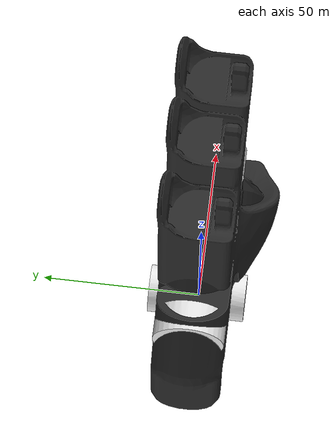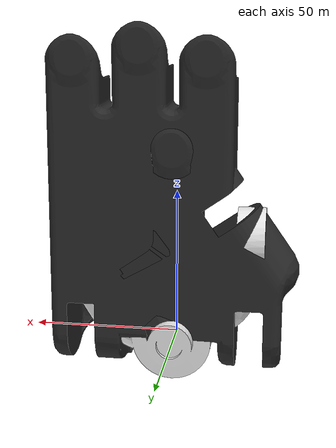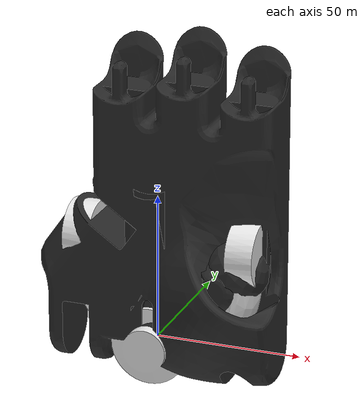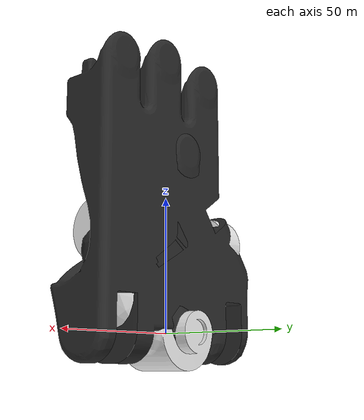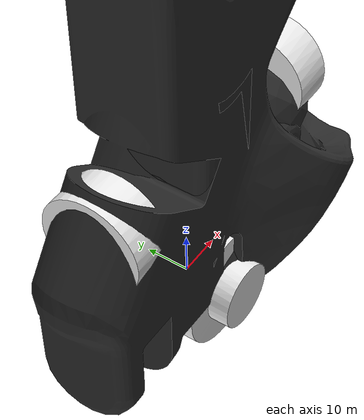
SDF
<?xml version="1.0" ?>
<sdf version='1.5'>
    <model name='shadowhand_motor'>
      <link name="world"/>
      <link name='rh_forearm'>
        <pose frame=''>0 0 0 0 -0 0</pose>
        <inertial>
          <pose frame=''>0 0 0.09 0 -0 0</pose>
          <mass>3</mass>
          <inertia>
            <ixx>0.0138</ixx>
            <ixy>0</ixy>
            <ixz>0</ixz>
            <iyy>0.0138</iyy>
            <iyz>0</iyz>
            <izz>0.00744</izz>
          </inertia>
        </inertial>
        <collision name='rh_forearm_collision'>
          <pose frame=''>0 0 0.092 0 -0 0</pose>
          <geometry>
            <cylinder>
              <length>0.0184</length>
              <radius>0.007</radius>
            </cylinder>
          </geometry>
          <surface>
            <contact>
              <ode/>
            </contact>
            <friction>
              <ode/>
              <torsional>
                <ode/>
              </torsional>
            </friction>
            <bounce/>
          </surface>
          <max_contacts>10</max_contacts>
        </collision>
        <collision name='rh_forearm_collision_1'>
          <pose frame=''>0 -0.01 0.181 0 0.78 0</pose>
          <geometry>
            <box>
              <size>0.007 0.007 0.007</size>
            </box>
          </geometry>
          <surface>
            <contact>
              <ode/>
            </contact>
            <friction>
              <ode/>
              <torsional>
                <ode/>
              </torsional>
            </friction>
            <bounce/>
          </surface>
          <max_contacts>10</max_contacts>
        </collision>
        <visual name='rh_forearm_visual'>
          <pose frame=''>0 0 0 0 -0 0</pose>
          <geometry>
            <mesh>
              <scale>0.1 0.1 0.1</scale>
              <uri>/home/brhm/DUC/RobotArm/src/my_arm/meshes/shadow_hand/hand/forearm.dae</uri>
            </mesh>
          </geometry>
          <material>
            <script>
              <uri>__default__</uri>
              <name>__default__</name>
            </script>
          </material>
        </visual>
        <gravity>1</gravity>
        <velocity_decay/>
        <self_collide>0</self_collide>
        <kinematic>0</kinematic>
      </link>
      <joint name='rh_world_joint' type='revolute'>
        <child>rh_forearm</child>
        <parent>world</parent>
        <axis>
          <limit>
            <lower>0</lower>
            <upper>0</upper>
          </limit>
          <dynamics>
            <damping>0.1</damping>
            <friction>0</friction>
            <spring_reference>0</spring_reference>
            <spring_stiffness>0</spring_stiffness>
          </dynamics>
          <use_parent_model_frame>0</use_parent_model_frame>
          <xyz>0 0 1</xyz>
        </axis>
      </joint>
      <link name='rh_wrist'>
        <pose frame=''>0 -0.01 0.213 0 -0 0</pose>
        <inertial>
          <pose frame=''>0 0 0.029 0 -0 0</pose>
          <mass>0.1</mass>
          <inertia>
            <ixx>3.5e-05</ixx>
            <ixy>0</ixy>
            <ixz>0</ixz>
            <iyy>6.4e-05</iyy>
            <iyz>0</iyz>
            <izz>4.38e-05</izz>
          </inertia>
        </inertial>
        <collision name='rh_wrist_collision'>
          <pose frame=''>0 0 0 -3.14159 1.57079 1.57079</pose>
          <geometry>
            <cylinder>
              <length>0.03</length>
              <radius>0.0135</radius>
            </cylinder>
          </geometry>
          <surface>
            <contact>
              <ode/>
            </contact>
            <friction>
              <ode/>
              <torsional>
                <ode/>
              </torsional>
            </friction>
            <bounce/>
          </surface>
          <max_contacts>10</max_contacts>
        </collision>
        <collision name='rh_wrist_collision_1'>
          <pose frame=''>-0.026 0 0.034 3.14159 1.57079 3.14159</pose>
          <geometry>
            <cylinder>
              <length>0.01</length>
              <radius>0.011</radius>
            </cylinder>
          </geometry>
          <surface>
            <contact>
              <ode/>
            </contact>
            <friction>
              <ode/>
              <torsional>
                <ode/>
              </torsional>
            </friction>
            <bounce/>
          </surface>
          <max_contacts>10</max_contacts>
        </collision>
        <collision name='rh_wrist_collision_2'>
          <pose frame=''>0.031 0 0.034 3.14159 1.57079 3.14159</pose>
          <geometry>
            <cylinder>
              <length>0.01</length>
              <radius>0.011</radius>
            </cylinder>
          </geometry>
          <surface>
            <contact>
              <ode/>
            </contact>
            <friction>
              <ode/>
              <torsional>
                <ode/>
              </torsional>
            </friction>
            <bounce/>
          </surface>
          <max_contacts>10</max_contacts>
        </collision>
        <collision name='rh_wrist_collision_3'>
          <pose frame=''>-0.021 0 0.011 0 0.7854 0</pose>
          <geometry>
            <box>
              <size>0.027 0.018 0.01</size>
            </box>
          </geometry>
          <surface>
            <contact>
              <ode/>
            </contact>
            <friction>
              <ode/>
              <torsional>
                <ode/>
              </torsional>
            </friction>
            <bounce/>
          </surface>
          <max_contacts>10</max_contacts>
        </collision>
        <collision name='rh_wrist_collision_4'>
          <pose frame=''>0.026 0 0.01 0 -0.7854 0</pose>
          <geometry>
            <box>
              <size>0.027 0.018 0.01</size>
            </box>
          </geometry>
          <surface>
            <contact>
              <ode/>
            </contact>
            <friction>
              <ode/>
              <torsional>
                <ode/>
              </torsional>
            </friction>
            <bounce/>
          </surface>
          <max_contacts>10</max_contacts>
        </collision>
        <visual name='rh_wrist_visual'>
          <pose frame=''>0 0 0 0 -0 0</pose>
          <geometry>
            <mesh>
              <scale>1 1 1</scale>
              <uri>/home/brhm/DUC/RobotArm/src/my_arm/meshes/shadow_hand/hand/wrist.dae</uri>
            </mesh>
          </geometry>
          <material>
            <script>
              <name>Gazebo/White</name>
              <uri>file://media/materials/scripts/gazebo.material</uri>
            </script>
          </material>
        </visual>
        <gravity>1</gravity>
        <velocity_decay/>
        <self_collide>0</self_collide>
        <kinematic>0</kinematic>
      </link>
      <joint name='rh_WRJ2' type='revolute'>
        <child>rh_wrist</child>
        <parent>rh_forearm</parent>
        <axis>
          <xyz>0 1 0</xyz>
          <limit>
            <lower>-0.523599</lower>
            <upper>0.174533</upper>
            <effort>10</effort>
            <velocity>2</velocity>
          </limit>
          <dynamics>
            <damping>0.1</damping>
            <friction>0</friction>
            <spring_reference>0</spring_reference>
            <spring_stiffness>0</spring_stiffness>
          </dynamics>
          <use_parent_model_frame>0</use_parent_model_frame>
        </axis>
        <physics>
          <provide_feedback>1</provide_feedback>
          <ode>
            <provide_feedback>1</provide_feedback>
            <implicit_spring_damper>1</implicit_spring_damper>
            <cfm_damping>1</cfm_damping>
            <limit>
              <cfm>0</cfm>
              <erp>0.2</erp>
            </limit>
          </ode>
        </physics>
      </joint>
      <link name='rh_palm'>
        <pose frame=''>0 -0.01 0.247 0 -0 0</pose>
        <inertial>
          <pose frame=''>0 0 0.035 0 -0 0</pose>
          <mass>0.3</mass>
          <inertia>
            <ixx>0.0003581</ixx>
            <ixy>0</ixy>
            <ixz>0</ixz>
            <iyy>0.0005287</iyy>
            <iyz>0</iyz>
            <izz>0.000191</izz>
          </inertia>
        </inertial>
        <collision name='rh_palm_collision'>
          <pose frame=''>0.011 0.0085 0.038 0 -0 0</pose>
          <geometry>
            <box>
              <size>0.062 0.007 0.098</size>
            </box>
          </geometry>
          <surface>
            <contact>
              <ode/>
            </contact>
            <friction>
              <ode/>
              <torsional>
                <ode/>
              </torsional>
            </friction>
            <bounce/>
          </surface>
          <max_contacts>10</max_contacts>
        </collision>
        <collision name='rh_palm_collision_1'>
          <pose frame=''>-0.002 -0.0035 0.038 0 -0 0</pose>
          <geometry>
            <box>
              <size>0.036 0.017 0.098</size>
            </box>
          </geometry>
          <surface>
            <contact>
              <ode/>
            </contact>
            <friction>
              <ode/>
              <torsional>
                <ode/>
              </torsional>
            </friction>
            <bounce/>
          </surface>
          <max_contacts>10</max_contacts>
        </collision>
        <collision name='rh_palm_collision_2'>
          <pose frame=''>0.029 -0.0035 0.082 0 -0 0</pose>
          <geometry>
            <box>
              <size>0.026 0.017 0.01</size>
            </box>
          </geometry>
          <surface>
            <contact>
              <ode/>
            </contact>
            <friction>
              <ode/>
              <torsional>
                <ode/>
              </torsional>
            </friction>
            <bounce/>
          </surface>
          <max_contacts>10</max_contacts>
        </collision>
        <collision name='rh_palm_collision_3'>
          <pose frame=''>0.0265 -0.001 0.07 0.2 -0 0.25</pose>
          <geometry>
            <box>
              <size>0.026 0.014 0.018</size>
            </box>
          </geometry>
          <surface>
            <contact>
              <ode/>
            </contact>
            <friction>
              <ode/>
              <torsional>
                <ode/>
              </torsional>
            </friction>
            <bounce/>
          </surface>
          <max_contacts>10</max_contacts>
        </collision>
        <collision name='rh_palm_collision_4'>
          <pose frame=''>0.0315 -0.0085 0.001 0 -0 0</pose>
          <geometry>
            <box>
              <size>0.021 0.027 0.024</size>
            </box>
          </geometry>
          <surface>
            <contact>
              <ode/>
            </contact>
            <friction>
              <ode/>
              <torsional>
                <ode/>
              </torsional>
            </friction>
            <bounce/>
          </surface>
          <max_contacts>10</max_contacts>
        </collision>
        <collision name='rh_palm_collision_5'>
          <pose frame=''>0.0125 -0.015 0.009 0 0 -0.48</pose>
          <geometry>
            <box>
              <size>0.022 0.005 0.04</size>
            </box>
          </geometry>
          <surface>
            <contact>
              <ode/>
            </contact>
            <friction>
              <ode/>
              <torsional>
                <ode/>
              </torsional>
            </friction>
            <bounce/>
          </surface>
          <max_contacts>10</max_contacts>
        </collision>
        <collision name='rh_palm_collision_6'>
          <pose frame=''>0.011 0 0.089 0 -0 0</pose>
          <geometry>
            <box>
              <size>0.018 0.024 0.004</size>
            </box>
          </geometry>
          <surface>
            <contact>
              <ode/>
            </contact>
            <friction>
              <ode/>
              <torsional>
                <ode/>
              </torsional>
            </friction>
            <bounce/>
          </surface>
          <max_contacts>10</max_contacts>
        </collision>
        <collision name='rh_palm_collision_7'>
          <pose frame=''>-0.03 0 0.009 0 -0 0</pose>
          <geometry>
            <box>
              <size>0.02 0.024 0.04</size>
            </box>
          </geometry>
          <surface>
            <contact>
              <ode/>
            </contact>
            <friction>
              <ode/>
              <torsional>
                <ode/>
              </torsional>
            </friction>
            <bounce/>
          </surface>
          <max_contacts>10</max_contacts>
        </collision>
        <visual name='rh_palm_visual'>
          <pose frame=''>0 0 0 0 -0 0</pose>
          <geometry>
            <mesh>
              <scale>1 1 1</scale>
              <uri>/home/brhm/DUC/RobotArm/src/my_arm/meshes/shadow_hand/hand/palm.dae</uri>
            </mesh>
          </geometry>
          <material>
            <script>
              <uri>__default__</uri>
              <name>__default__</name>
            </script>
          </material>
        </visual>
        <gravity>1</gravity>
        <velocity_decay/>
        <self_collide>0</self_collide>
        <sensor name='rh_palm_contact' type='contact'>
          <always_on>1</always_on>
          <update_rate>1000</update_rate>
          <contact>
            <collision>rh_palm_collision</collision>
            <topic>rh_palm_collision</topic>
          </contact>
          <plugin name='rh_palm_gazebo_ros_bumper_controller' filename='libgazebo_ros_bumper.so'>
            <alwaysOn>true</alwaysOn>
            <frameName>rh_palm</frameName>
            <updateRate>100.0</updateRate>
            <bumperTopicName>contacts/rh_palm</bumperTopicName>
            <robotNamespace>/</robotNamespace>
          </plugin>
        </sensor>
        <kinematic>0</kinematic>
      </link>
      <joint name='rh_WRJ1' type='revolute'>
        <child>rh_palm</child>
        <parent>rh_wrist</parent>
        <axis>
          <xyz>1 0 0</xyz>
          <limit>
            <lower>-0.698132</lower>
            <upper>0.488692</upper>
            <effort>30</effort>
            <velocity>2</velocity>
          </limit>
          <dynamics>
            <damping>0.1</damping>
            <friction>0</friction>
            <spring_reference>0</spring_reference>
            <spring_stiffness>0</spring_stiffness>
          </dynamics>
          <use_parent_model_frame>0</use_parent_model_frame>
        </axis>
        <physics>
          <provide_feedback>1</provide_feedback>
          <ode>
            <provide_feedback>1</provide_feedback>
            <implicit_spring_damper>1</implicit_spring_damper>
            <cfm_damping>1</cfm_damping>
            <limit>
              <cfm>0</cfm>
              <erp>0.2</erp>
            </limit>
          </ode>
        </physics>
      </joint>
      <link name='rh_ffknuckle'>
        <pose frame=''>0.033 -0.01 0.342 0 -0 0</pose>
        <inertial>
          <pose frame=''>0 0 0 0 -0 0</pose>
          <mass>0.008</mass>
          <inertia>
            <ixx>2.6e-07</ixx>
            <ixy>0</ixy>
            <ixz>0</ixz>
            <iyy>2.6e-07</iyy>
            <iyz>0</iyz>
            <izz>3.2e-07</izz>
          </inertia>
        </inertial>
        <collision name='rh_ffknuckle_collision'>
          <pose frame=''>0 0 0 3.14159 1.57079 3.14159</pose>
          <geometry>
            <cylinder>
              <length>0.014</length>
              <radius>0.007</radius>
            </cylinder>
          </geometry>
          <surface>
            <contact>
              <ode/>
            </contact>
            <friction>
              <ode/>
              <torsional>
                <ode/>
              </torsional>
            </friction>
            <bounce/>
          </surface>
          <max_contacts>10</max_contacts>
        </collision>
        <visual name='rh_ffknuckle_visual'>
          <pose frame=''>0 0 0.0005 0 -0 0</pose>
          <geometry>
            <mesh>
              <scale>1 1 1</scale>
              <uri>/home/brhm/DUC/RobotArm/src/my_arm/meshes/shadow_hand/hand/knuckle.dae</uri>
            </mesh>
          </geometry>
          <material>
            <script>
              <name>Gazebo/Grey</name>
              <uri>file://media/materials/scripts/gazebo.material</uri>
            </script>
          </material>
        </visual>
        <gravity>1</gravity>
        <velocity_decay/>
        <self_collide>0</self_collide>
        <sensor name='rh_ffknuckle_contact' type='contact'>
          <always_on>1</always_on>
          <update_rate>1000</update_rate>
          <contact>
            <collision>rh_ffknuckle_collision</collision>
            <topic>rh_ffknuckle_collision</topic>
          </contact>
          <plugin name='rh_ffknuckle_gazebo_ros_bumper_controller' filename='libgazebo_ros_bumper.so'>
            <alwaysOn>true</alwaysOn>
            <frameName>rh_ffknuckle</frameName>
            <updateRate>100.0</updateRate>
            <bumperTopicName>contacts/rh_ff/knuckle</bumperTopicName>
            <robotNamespace>/</robotNamespace>
          </plugin>
        </sensor>
        <kinematic>0</kinematic>
      </link>
      <joint name='rh_FFJ4' type='revolute'>
        <child>rh_ffknuckle</child>
        <parent>rh_palm</parent>
        <axis>
          <xyz>0 -1 0</xyz>
          <limit>
            <lower>-0.349066</lower>
            <upper>0.349066</upper>
            <effort>2</effort>
            <velocity>2</velocity>
          </limit>
          <dynamics>
            <damping>0.1</damping>
            <friction>0</friction>
            <spring_reference>0</spring_reference>
            <spring_stiffness>0</spring_stiffness>
          </dynamics>
          <use_parent_model_frame>0</use_parent_model_frame>
        </axis>
        <physics>
          <provide_feedback>1</provide_feedback>
          <ode>
            <provide_feedback>1</provide_feedback>
            <implicit_spring_damper>1</implicit_spring_damper>
            <cfm_damping>1</cfm_damping>
            <limit>
              <cfm>0</cfm>
              <erp>0.2</erp>
            </limit>
          </ode>
        </physics>
      </joint>
      <link name='rh_ffproximal'>
        <pose frame=''>0.033 -0.01 0.342 0 -0 0</pose>
        <inertial>
          <pose frame=''>0 0 0.0225 0 -0 0</pose>
          <mass>0.03</mass>
          <inertia>
            <ixx>9.8e-06</ixx>
            <ixy>0</ixy>
            <ixz>0</ixz>
            <iyy>1e-05</iyy>
            <iyz>0</iyz>
            <izz>1.8e-06</izz>
          </inertia>
        </inertial>
        <collision name='rh_ffproximal_collision'>
          <pose frame=''>0 0 0.025 0 -0 0</pose>
          <geometry>
            <cylinder>
              <length>0.04</length>
              <radius>0.007</radius>
            </cylinder>
          </geometry>
          <surface>
            <contact>
              <ode/>
            </contact>
            <friction>
              <ode/>
              <torsional>
                <ode/>
              </torsional>
            </friction>
            <bounce/>
          </surface>
          <max_contacts>10</max_contacts>
        </collision>
        <visual name='rh_ffproximal_visual'>
          <pose frame=''>0 0 0 0 -0 0</pose>
          <geometry>
            <mesh>
              <scale>1 1 1</scale>
              <uri>/home/brhm/DUC/RobotArm/src/my_arm/meshes/shadow_hand/hand/F3.dae</uri>
            </mesh>
          </geometry>
          <material>
            <script>
              <uri>__default__</uri>
              <name>__default__</name>
            </script>
          </material>
        </visual>
        <gravity>1</gravity>
        <velocity_decay/>
        <self_collide>1</self_collide>
        <sensor name='rh_ffproximal_contact' type='contact'>
          <always_on>1</always_on>
          <update_rate>1000</update_rate>
          <contact>
            <collision>rh_ffproximal_collision</collision>
            <topic>rh_ffproximal_collision</topic>
          </contact>
          <plugin name='rh_ffproximal_gazebo_ros_bumper_controller' filename='libgazebo_ros_bumper.so'>
            <alwaysOn>true</alwaysOn>
            <frameName>rh_ffproximal</frameName>
            <updateRate>100.0</updateRate>
            <bumperTopicName>contacts/rh_ff/proximal</bumperTopicName>
            <robotNamespace>/</robotNamespace>
          </plugin>
        </sensor>
        <kinematic>0</kinematic>
      </link>
      <joint name='rh_FFJ3' type='revolute'>
        <child>rh_ffproximal</child>
        <parent>rh_ffknuckle</parent>
        <axis>
          <xyz>1 0 0</xyz>
          <limit>
            <lower>0</lower>
            <upper>1.5708</upper>
            <effort>2</effort>
            <velocity>2</velocity>
          </limit>
          <dynamics>
            <damping>0.1</damping>
            <friction>0</friction>
            <spring_reference>0</spring_reference>
            <spring_stiffness>0</spring_stiffness>
          </dynamics>
          <use_parent_model_frame>0</use_parent_model_frame>
        </axis>
        <physics>
          <provide_feedback>1</provide_feedback>
          <ode>
            <provide_feedback>1</provide_feedback>
            <implicit_spring_damper>1</implicit_spring_damper>
            <cfm_damping>1</cfm_damping>
            <limit>
              <cfm>0</cfm>
              <erp>0.2</erp>
            </limit>
          </ode>
        </physics>
      </joint>
      <link name='rh_ffmiddle'>
        <pose frame=''>0.033 -0.01 0.387 0 -0 0</pose>
        <inertial>
          <pose frame=''>0 0 0.0125 0 -0 0</pose>
          <mass>0.017</mass>
          <inertia>
            <ixx>2.6e-06</ixx>
            <ixy>0</ixy>
            <ixz>0</ixz>
            <iyy>2.7e-06</iyy>
            <iyz>0</iyz>
            <izz>8.7e-07</izz>
          </inertia>
        </inertial>
        <collision name='rh_ffmiddle_collision'>
          <pose frame=''>0 0 0.0125 0 -0 0</pose>
          <geometry>
            <cylinder>
              <length>0.025</length>
              <radius>0.007</radius>
            </cylinder>
          </geometry>
          <surface>
            <contact>
              <ode/>
            </contact>
            <friction>
              <ode/>
              <torsional>
                <ode/>
              </torsional>
            </friction>
            <bounce/>
          </surface>
          <max_contacts>10</max_contacts>
        </collision>
        <collision name='rh_ffmiddle_collision_1'>
          <pose frame=''>0 0 0 0 -0 0</pose>
          <geometry>
            <sphere>
              <radius>0.007</radius>
            </sphere>
          </geometry>
          <surface>
            <contact>
              <ode/>
            </contact>
            <friction>
              <ode/>
              <torsional>
                <ode/>
              </torsional>
            </friction>
            <bounce/>
          </surface>
          <max_contacts>10</max_contacts>
        </collision>
        <collision name='rh_ffmiddle_collision_2'>
          <pose frame=''>0 0 0.025 0 -0 0</pose>
          <geometry>
            <sphere>
              <radius>0.007</radius>
            </sphere>
          </geometry>
          <surface>
            <contact>
              <ode/>
            </contact>
            <friction>
              <ode/>
              <torsional>
                <ode/>
              </torsional>
            </friction>
            <bounce/>
          </surface>
          <max_contacts>10</max_contacts>
        </collision>
        <visual name='rh_ffmiddle_visual'>
          <pose frame=''>0 0 0 0 -0 0</pose>
          <geometry>
            <mesh>
              <scale>1 1 1</scale>
              <uri>/home/brhm/DUC/RobotArm/src/my_arm/meshes/shadow_hand/hand/F2.dae</uri>
            </mesh>
          </geometry>
          <material>
            <script>
              <uri>__default__</uri>
              <name>__default__</name>
            </script>
          </material>
        </visual>
        <gravity>1</gravity>
        <velocity_decay/>
        <self_collide>1</self_collide>
        <sensor name='rh_ffmiddle_contact' type='contact'>
          <always_on>1</always_on>
          <update_rate>1000</update_rate>
          <contact>
            <collision>rh_ffmiddle_collision</collision>
            <topic>rh_ffmiddle_collision</topic>
          </contact>
          <plugin name='rh_ffproximal_gazebo_ros_bumper_controller' filename='libgazebo_ros_bumper.so'>
            <alwaysOn>true</alwaysOn>
            <frameName>rh_ffmiddle</frameName>
            <updateRate>100.0</updateRate>
            <bumperTopicName>contacts/rh_ff/middle</bumperTopicName>
            <robotNamespace>/</robotNamespace>
          </plugin>
        </sensor>
        <kinematic>0</kinematic>
      </link>
      <joint name='rh_FFJ2' type='revolute'>
        <child>rh_ffmiddle</child>
        <parent>rh_ffproximal</parent>
        <axis>
          <xyz>1 0 0</xyz>
          <limit>
            <lower>0</lower>
            <upper>1.5708</upper>
            <effort>2</effort>
            <velocity>2</velocity>
          </limit>
          <dynamics>
            <damping>0.1</damping>
            <friction>0</friction>
            <spring_reference>0</spring_reference>
            <spring_stiffness>0</spring_stiffness>
          </dynamics>
          <use_parent_model_frame>0</use_parent_model_frame>
        </axis>
        <physics>
          <provide_feedback>1</provide_feedback>
          <ode>
            <provide_feedback>1</provide_feedback>
            <implicit_spring_damper>1</implicit_spring_damper>
            <cfm_damping>1</cfm_damping>
            <limit>
              <cfm>0</cfm>
              <erp>0.2</erp>
            </limit>
          </ode>
        </physics>
      </joint>
      <link name='rh_ffdistal'>
        <pose frame=''>0.033 -0.01 0.412 0 -0 0</pose>
        <inertial>
          <pose frame=''>0 0 0.013077 0 -0 0</pose>
          <mass>0.013</mass>
          <inertia>
            <ixx>1.12092e-06</ixx>
            <ixy>0</ixy>
            <ixz>0</ixz>
            <iyy>1.28092e-06</iyy>
            <iyz>0</iyz>
            <izz>5.3e-07</izz>
          </inertia>
        </inertial>
        <collision name='rh_ffdistal_collision'>
          <pose frame=''>0 0 0 0 -0 0</pose>
          <geometry>
            <mesh>
              <scale>1 1 1</scale>
              <uri>/home/brhm/DUC/RobotArm/src/my_arm/meshes/shadow_hand/hand/F1.dae</uri>
            </mesh>
          </geometry>
          <surface>
            <contact>
              <ode>
                <kp>1e+07</kp>
                <kd>1</kd>
              </ode>
            </contact>
            <friction>
              <ode>
                <mu>500</mu>
                <mu2>500</mu2>
              </ode>
              <torsional>
                <ode/>
              </torsional>
            </friction>
            <bounce/>
          </surface>
          <max_contacts>10</max_contacts>
        </collision>
        <visual name='rh_ffdistal_visual'>
          <pose frame=''>0 0 0 0 -0 0</pose>
          <geometry>
            <mesh>
              <scale>1 1 1</scale>
              <uri>/home/brhm/DUC/RobotArm/src/my_arm/meshes/shadow_hand/hand/F1.dae</uri>
            </mesh>
          </geometry>
          <material>
            <script>
              <uri>__default__</uri>
              <name>__default__</name>
            </script>
          </material>
        </visual>
        <gravity>1</gravity>
        <velocity_decay/>
        <self_collide>1</self_collide>
        <sensor name='rh_ffdistal_contact' type='contact'>
          <always_on>1</always_on>
          <update_rate>1000</update_rate>
          <contact>
            <collision>rh_ffdistal_collision</collision>
            <topic>rh_ffdistal_collision</topic>
          </contact>
          <plugin name='rh_ffdistal_gazebo_ros_bumper_controller' filename='libgazebo_ros_bumper.so'>
            <alwaysOn>true</alwaysOn>
            <frameName>rh_ffdistal</frameName>
            <updateRate>100.0</updateRate>
            <bumperTopicName>contacts/rh_ff/distal</bumperTopicName>
            <robotNamespace>/</robotNamespace>
          </plugin>
        </sensor>
        <kinematic>0</kinematic>
      </link>
      <joint name='rh_FFJ1' type='revolute'>
        <child>rh_ffdistal</child>
        <parent>rh_ffmiddle</parent>
        <axis>
          <xyz>1 0 0</xyz>
          <limit>
            <lower>0</lower>
            <upper>1.5708</upper>
            <effort>2</effort>
            <velocity>2</velocity>
          </limit>
          <dynamics>
            <damping>0.1</damping>
            <friction>0</friction>
            <spring_reference>0</spring_reference>
            <spring_stiffness>0</spring_stiffness>
          </dynamics>
          <use_parent_model_frame>0</use_parent_model_frame>
        </axis>
        <physics>
          <provide_feedback>1</provide_feedback>
          <ode>
            <provide_feedback>1</provide_feedback>
            <implicit_spring_damper>1</implicit_spring_damper>
            <cfm_damping>1</cfm_damping>
            <limit>
              <cfm>0</cfm>
              <erp>0.2</erp>
            </limit>
          </ode>
        </physics>
      </joint>
      <link name='rh_lfmetacarpal'>
        <pose frame=''>-0.033 -0.01 0.26771 0 -0 0</pose>
        <inertial>
          <pose frame=''>0 0 0.04 0 -0 0</pose>
          <mass>0.03</mass>
          <inertia>
            <ixx>1.45e-05</ixx>
            <ixy>0</ixy>
            <ixz>0</ixz>
            <iyy>1.638e-05</iyy>
            <iyz>0</iyz>
            <izz>4.272e-06</izz>
          </inertia>
        </inertial>
        <collision name='rh_lfmetacarpal_collision'>
          <pose frame=''>0 0 0.038 0 -0 0</pose>
          <geometry>
            <box>
              <size>0.018 0.024 0.04</size>
            </box>
          </geometry>
          <surface>
            <contact>
              <ode/>
            </contact>
            <friction>
              <ode/>
              <torsional>
                <ode/>
              </torsional>
            </friction>
            <bounce/>
          </surface>
          <max_contacts>10</max_contacts>
        </collision>
        <visual name='rh_lfmetacarpal_visual'>
          <pose frame=''>0 0 0 0 -0 0</pose>
          <geometry>
            <mesh>
              <scale>1 1 1</scale>
              <uri>/home/brhm/DUC/RobotArm/src/my_arm/meshes/shadow_hand/hand/lfmetacarpal.dae</uri>
            </mesh>
          </geometry>
          <material>
            <script>
              <uri>__default__</uri>
              <name>__default__</name>
            </script>
          </material>
        </visual>
        <gravity>1</gravity>
        <velocity_decay/>
        <self_collide>1</self_collide>
        <sensor name='rh_lfmetacarpal_contact' type='contact'>
          <always_on>1</always_on>
          <update_rate>1000</update_rate>
          <contact>
            <collision>rh_lfmetacarpal_collision</collision>
            <topic>rh_lfmetacarpal_collision</topic>
          </contact>
          <plugin name='rh_lfmetacarpal_gazebo_ros_bumper_controller' filename='libgazebo_ros_bumper.so'>
            <alwaysOn>true</alwaysOn>
            <frameName>rh_lfmetacarpal</frameName>
            <updateRate>100.0</updateRate>
            <bumperTopicName>contacts/rh_lf/metacarpal</bumperTopicName>
            <robotNamespace>/</robotNamespace>
          </plugin>
        </sensor>
        <kinematic>0</kinematic>
      </link>
      <joint name='rh_LFJ5' type='revolute'>
        <child>rh_lfmetacarpal</child>
        <parent>rh_palm</parent>
        <axis>
          <xyz>0.573576 0 0.819152</xyz>
          <limit>
            <lower>0</lower>
            <upper>0.785398</upper>
            <effort>2</effort>
            <velocity>2</velocity>
          </limit>
          <dynamics>
            <damping>0.1</damping>
            <friction>0</friction>
            <spring_reference>0</spring_reference>
            <spring_stiffness>0</spring_stiffness>
          </dynamics>
          <use_parent_model_frame>0</use_parent_model_frame>
        </axis>
        <physics>
          <provide_feedback>1</provide_feedback>
          <ode>
            <provide_feedback>1</provide_feedback>
            <implicit_spring_damper>1</implicit_spring_damper>
            <cfm_damping>1</cfm_damping>
            <limit>
              <cfm>0</cfm>
              <erp>0.2</erp>
            </limit>
          </ode>
        </physics>
      </joint>
      <link name='rh_lfknuckle'>
        <pose frame=''>-0.033 -0.01 0.3335 0 -0 0</pose>
        <inertial>
          <pose frame=''>0 0 0 0 -0 0</pose>
          <mass>0.008</mass>
          <inertia>
            <ixx>2.6e-07</ixx>
            <ixy>0</ixy>
            <ixz>0</ixz>
            <iyy>2.6e-07</iyy>
            <iyz>0</iyz>
            <izz>3.2e-07</izz>
          </inertia>
        </inertial>
        <collision name='rh_lfknuckle_collision'>
          <pose frame=''>0 0 0 3.14159 1.57079 3.14159</pose>
          <geometry>
            <cylinder>
              <length>0.014</length>
              <radius>0.007</radius>
            </cylinder>
          </geometry>
          <surface>
            <contact>
              <ode/>
            </contact>
            <friction>
              <ode/>
              <torsional>
                <ode/>
              </torsional>
            </friction>
            <bounce/>
          </surface>
          <max_contacts>10</max_contacts>
        </collision>
        <visual name='rh_lfknuckle_visual'>
          <pose frame=''>0 0 0.0005 0 -0 0</pose>
          <geometry>
            <mesh>
              <scale>1 1 1</scale>
              <uri>/home/brhm/DUC/RobotArm/src/my_arm/meshes/shadow_hand/hand/knuckle.dae</uri>
            </mesh>
          </geometry>
          <material>
            <script>
              <name>Gazebo/Grey</name>
              <uri>file://media/materials/scripts/gazebo.material</uri>
            </script>
          </material>
        </visual>
        <gravity>1</gravity>
        <velocity_decay/>
        <self_collide>0</self_collide>
        <sensor name='rh_lfknuckle_contact' type='contact'>
          <always_on>1</always_on>
          <update_rate>1000</update_rate>
          <contact>
            <collision>rh_lfknuckle_collision</collision>
            <topic>rh_lfknuckle_collision</topic>
          </contact>
          <plugin name='rh_lfknuckle_gazebo_ros_bumper_controller' filename='libgazebo_ros_bumper.so'>
            <alwaysOn>true</alwaysOn>
            <frameName>rh_lfknuckle</frameName>
            <updateRate>100.0</updateRate>
            <bumperTopicName>contacts/rh_lf/knuckle</bumperTopicName>
            <robotNamespace>/</robotNamespace>
          </plugin>
        </sensor>
        <kinematic>0</kinematic>
      </link>
      <joint name='rh_LFJ4' type='revolute'>
        <child>rh_lfknuckle</child>
        <parent>rh_lfmetacarpal</parent>
        <axis>
          <xyz>0 1 0</xyz>
          <limit>
            <lower>-0.349066</lower>
            <upper>0.349066</upper>
            <effort>2</effort>
            <velocity>2</velocity>
          </limit>
          <dynamics>
            <damping>0.1</damping>
            <friction>0</friction>
            <spring_reference>0</spring_reference>
            <spring_stiffness>0</spring_stiffness>
          </dynamics>
          <use_parent_model_frame>0</use_parent_model_frame>
        </axis>
        <physics>
          <provide_feedback>1</provide_feedback>
          <ode>
            <provide_feedback>1</provide_feedback>
            <implicit_spring_damper>1</implicit_spring_damper>
            <cfm_damping>1</cfm_damping>
            <limit>
              <cfm>0</cfm>
              <erp>0.2</erp>
            </limit>
          </ode>
        </physics>
      </joint>
      <link name='rh_lfproximal'>
        <pose frame=''>-0.033 -0.01 0.3335 0 -0 0</pose>
        <inertial>
          <pose frame=''>0 0 0.0225 0 -0 0</pose>
          <mass>0.03</mass>
          <inertia>
            <ixx>9.8e-06</ixx>
            <ixy>0</ixy>
            <ixz>0</ixz>
            <iyy>1e-05</iyy>
            <iyz>0</iyz>
            <izz>1.8e-06</izz>
          </inertia>
        </inertial>
        <collision name='rh_lfproximal_collision'>
          <pose frame=''>0 0 0.025 0 -0 0</pose>
          <geometry>
            <cylinder>
              <length>0.04</length>
              <radius>0.007</radius>
            </cylinder>
          </geometry>
          <surface>
            <contact>
              <ode/>
            </contact>
            <friction>
              <ode/>
              <torsional>
                <ode/>
              </torsional>
            </friction>
            <bounce/>
          </surface>
          <max_contacts>10</max_contacts>
        </collision>
        <visual name='rh_lfproximal_visual'>
          <pose frame=''>0 0 0 0 -0 0</pose>
          <geometry>
            <mesh>
              <scale>1 1 1</scale>
              <uri>/home/brhm/DUC/RobotArm/src/my_arm/meshes/shadow_hand/hand/F3.dae</uri>
            </mesh>
          </geometry>
          <material>
            <script>
              <uri>__default__</uri>
              <name>__default__</name>
            </script>
          </material>
        </visual>
        <gravity>1</gravity>
        <velocity_decay/>
        <self_collide>1</self_collide>
        <sensor name='rh_lfproximal_contact' type='contact'>
          <always_on>1</always_on>
          <update_rate>1000</update_rate>
          <contact>
            <collision>rh_lfproximal_collision</collision>
            <topic>rh_lfproximal_collision</topic>
          </contact>
          <plugin name='rh_lfproximal_gazebo_ros_bumper_controller' filename='libgazebo_ros_bumper.so'>
            <alwaysOn>true</alwaysOn>
            <frameName>rh_lfproximal</frameName>
            <updateRate>100.0</updateRate>
            <bumperTopicName>contacts/rh_lf/proximal</bumperTopicName>
            <robotNamespace>/</robotNamespace>
          </plugin>
        </sensor>
        <kinematic>0</kinematic>
      </link>
      <joint name='rh_LFJ3' type='revolute'>
        <child>rh_lfproximal</child>
        <parent>rh_lfknuckle</parent>
        <axis>
          <xyz>1 0 0</xyz>
          <limit>
            <lower>0</lower>
            <upper>1.5708</upper>
            <effort>2</effort>
            <velocity>2</velocity>
          </limit>
          <dynamics>
            <damping>0.1</damping>
            <friction>0</friction>
            <spring_reference>0</spring_reference>
            <spring_stiffness>0</spring_stiffness>
          </dynamics>
          <use_parent_model_frame>0</use_parent_model_frame>
        </axis>
        <physics>
          <provide_feedback>1</provide_feedback>
          <ode>
            <provide_feedback>1</provide_feedback>
            <implicit_spring_damper>1</implicit_spring_damper>
            <cfm_damping>1</cfm_damping>
            <limit>
              <cfm>0</cfm>
              <erp>0.2</erp>
            </limit>
          </ode>
        </physics>
      </joint>
      <link name='rh_lfmiddle'>
        <pose frame=''>-0.033 -0.01 0.3785 0 -0 0</pose>
        <inertial>
          <pose frame=''>0 0 0.0125 0 -0 0</pose>
          <mass>0.017</mass>
          <inertia>
            <ixx>2.6e-06</ixx>
            <ixy>0</ixy>
            <ixz>0</ixz>
            <iyy>2.7e-06</iyy>
            <iyz>0</iyz>
            <izz>8.7e-07</izz>
          </inertia>
        </inertial>
        <collision name='rh_lfmiddle_collision'>
          <pose frame=''>0 0 0.0125 0 -0 0</pose>
          <geometry>
            <cylinder>
              <length>0.025</length>
              <radius>0.007</radius>
            </cylinder>
          </geometry>
          <surface>
            <contact>
              <ode/>
            </contact>
            <friction>
              <ode/>
              <torsional>
                <ode/>
              </torsional>
            </friction>
            <bounce/>
          </surface>
          <max_contacts>10</max_contacts>
        </collision>
        <collision name='rh_lfmiddle_collision_1'>
          <pose frame=''>0 0 0 0 -0 0</pose>
          <geometry>
            <sphere>
              <radius>0.007</radius>
            </sphere>
          </geometry>
          <surface>
            <contact>
              <ode/>
            </contact>
            <friction>
              <ode/>
              <torsional>
                <ode/>
              </torsional>
            </friction>
            <bounce/>
          </surface>
          <max_contacts>10</max_contacts>
        </collision>
        <collision name='rh_lfmiddle_collision_2'>
          <pose frame=''>0 0 0.025 0 -0 0</pose>
          <geometry>
            <sphere>
              <radius>0.007</radius>
            </sphere>
          </geometry>
          <surface>
            <contact>
              <ode/>
            </contact>
            <friction>
              <ode/>
              <torsional>
                <ode/>
              </torsional>
            </friction>
            <bounce/>
          </surface>
          <max_contacts>10</max_contacts>
        </collision>
        <visual name='rh_lfmiddle_visual'>
          <pose frame=''>0 0 0 0 -0 0</pose>
          <geometry>
            <mesh>
              <scale>1 1 1</scale>
              <uri>/home/brhm/DUC/RobotArm/src/my_arm/meshes/shadow_hand/hand/F2.dae</uri>
            </mesh>
          </geometry>
          <material>
            <script>
              <uri>__default__</uri>
              <name>__default__</name>
            </script>
          </material>
        </visual>
        <gravity>1</gravity>
        <velocity_decay/>
        <self_collide>1</self_collide>
        <sensor name='rh_lfmiddle_contact' type='contact'>
          <always_on>1</always_on>
          <update_rate>1000</update_rate>
          <contact>
            <collision>rh_lfmiddle_collision</collision>
            <topic>rh_lfmiddle_collision</topic>
          </contact>
          <plugin name='rh_lfproximal_gazebo_ros_bumper_controller' filename='libgazebo_ros_bumper.so'>
            <alwaysOn>true</alwaysOn>
            <frameName>rh_lfmiddle</frameName>
            <updateRate>100.0</updateRate>
            <bumperTopicName>contacts/rh_lf/middle</bumperTopicName>
            <robotNamespace>/</robotNamespace>
          </plugin>
        </sensor>
        <kinematic>0</kinematic>
      </link>
      <joint name='rh_LFJ2' type='revolute'>
        <child>rh_lfmiddle</child>
        <parent>rh_lfproximal</parent>
        <axis>
          <xyz>1 0 0</xyz>
          <limit>
            <lower>0</lower>
            <upper>1.5708</upper>
            <effort>2</effort>
            <velocity>2</velocity>
          </limit>
          <dynamics>
            <damping>0.1</damping>
            <friction>0</friction>
            <spring_reference>0</spring_reference>
            <spring_stiffness>0</spring_stiffness>
          </dynamics>
          <use_parent_model_frame>0</use_parent_model_frame>
        </axis>
        <physics>
          <provide_feedback>1</provide_feedback>
          <ode>
            <provide_feedback>1</provide_feedback>
            <implicit_spring_damper>1</implicit_spring_damper>
            <cfm_damping>1</cfm_damping>
            <limit>
              <cfm>0</cfm>
              <erp>0.2</erp>
            </limit>
          </ode>
        </physics>
      </joint>
      <link name='rh_lfdistal'>
        <pose frame=''>-0.033 -0.01 0.4035 0 -0 0</pose>
        <inertial>
          <pose frame=''>0 0 0.013077 0 -0 0</pose>
          <mass>0.013</mass>
          <inertia>
            <ixx>1.12092e-06</ixx>
            <ixy>0</ixy>
            <ixz>0</ixz>
            <iyy>1.28092e-06</iyy>
            <iyz>0</iyz>
            <izz>5.3e-07</izz>
          </inertia>
        </inertial>
        <collision name='rh_lfdistal_collision'>
          <pose frame=''>0 0 0 0 -0 0</pose>
          <geometry>
            <mesh>
              <scale>1 1 1</scale>
              <uri>/home/brhm/DUC/RobotArm/src/my_arm/meshes/shadow_hand/hand/F1.dae</uri>
            </mesh>
          </geometry>
          <surface>
            <contact>
              <ode>
                <kp>1e+07</kp>
                <kd>1</kd>
              </ode>
            </contact>
            <friction>
              <ode>
                <mu>500</mu>
                <mu2>500</mu2>
              </ode>
              <torsional>
                <ode/>
              </torsional>
            </friction>
            <bounce/>
          </surface>
          <max_contacts>10</max_contacts>
        </collision>
        <visual name='rh_lfdistal_visual'>
          <pose frame=''>0 0 0 0 -0 0</pose>
          <geometry>
            <mesh>
              <scale>1 1 1</scale>
              <uri>/home/brhm/DUC/RobotArm/src/my_arm/meshes/shadow_hand/hand/F1.dae</uri>
            </mesh>
          </geometry>
          <material>
            <script>
              <uri>__default__</uri>
              <name>__default__</name>
            </script>
          </material>
        </visual>
        <gravity>1</gravity>
        <velocity_decay/>
        <self_collide>1</self_collide>
        <sensor name='rh_lfdistal_contact' type='contact'>
          <always_on>1</always_on>
          <update_rate>1000</update_rate>
          <contact>
            <collision>rh_lfdistal_collision</collision>
            <topic>rh_lfdistal_collision</topic>
          </contact>
          <plugin name='rh_lfdistal_gazebo_ros_bumper_controller' filename='libgazebo_ros_bumper.so'>
            <alwaysOn>true</alwaysOn>
            <frameName>rh_lfdistal</frameName>
            <updateRate>100.0</updateRate>
            <bumperTopicName>contacts/rh_lf/distal</bumperTopicName>
            <robotNamespace>/</robotNamespace>
          </plugin>
        </sensor>
        <kinematic>0</kinematic>
      </link>
      <joint name='rh_LFJ1' type='revolute'>
        <child>rh_lfdistal</child>
        <parent>rh_lfmiddle</parent>
        <axis>
          <xyz>1 0 0</xyz>
          <limit>
            <lower>0</lower>
            <upper>1.5708</upper>
            <effort>2</effort>
            <velocity>2</velocity>
          </limit>
          <dynamics>
            <damping>0.1</damping>
            <friction>0</friction>
            <spring_reference>0</spring_reference>
            <spring_stiffness>0</spring_stiffness>
          </dynamics>
          <use_parent_model_frame>0</use_parent_model_frame>
        </axis>
        <physics>
          <provide_feedback>1</provide_feedback>
          <ode>
            <provide_feedback>1</provide_feedback>
            <implicit_spring_damper>1</implicit_spring_damper>
            <cfm_damping>1</cfm_damping>
            <limit>
              <cfm>0</cfm>
              <erp>0.2</erp>
            </limit>
          </ode>
        </physics>
      </joint>
      <link name='rh_mfknuckle'>
        <pose frame=''>0.011 -0.01 0.346 0 -0 0</pose>
        <inertial>
          <pose frame=''>0 0 0 0 -0 0</pose>
          <mass>0.008</mass>
          <inertia>
            <ixx>2.6e-07</ixx>
            <ixy>0</ixy>
            <ixz>0</ixz>
            <iyy>2.6e-07</iyy>
            <iyz>0</iyz>
            <izz>3.2e-07</izz>
          </inertia>
        </inertial>
        <collision name='rh_mfknuckle_collision'>
          <pose frame=''>0 0 0 3.14159 1.57079 3.14159</pose>
          <geometry>
            <cylinder>
              <length>0.014</length>
              <radius>0.007</radius>
            </cylinder>
          </geometry>
          <surface>
            <contact>
              <ode/>
            </contact>
            <friction>
              <ode/>
              <torsional>
                <ode/>
              </torsional>
            </friction>
            <bounce/>
          </surface>
          <max_contacts>10</max_contacts>
        </collision>
        <visual name='rh_mfknuckle_visual'>
          <pose frame=''>0 0 0.0005 0 -0 0</pose>
          <geometry>
            <mesh>
              <scale>1 1 1</scale>
              <uri>/home/brhm/DUC/RobotArm/src/my_arm/meshes/shadow_hand/hand/knuckle.dae</uri>
            </mesh>
          </geometry>
          <material>
            <script>
              <name>Gazebo/Grey</name>
              <uri>file://media/materials/scripts/gazebo.material</uri>
            </script>
          </material>
        </visual>
        <gravity>1</gravity>
        <velocity_decay/>
        <self_collide>0</self_collide>
        <sensor name='rh_mfknuckle_contact' type='contact'>
          <always_on>1</always_on>
          <update_rate>1000</update_rate>
          <contact>
            <collision>rh_mfknuckle_collision</collision>
            <topic>rh_mfknuckle_collision</topic>
          </contact>
          <plugin name='rh_mfknuckle_gazebo_ros_bumper_controller' filename='libgazebo_ros_bumper.so'>
            <alwaysOn>true</alwaysOn>
            <frameName>rh_mfknuckle</frameName>
            <updateRate>100.0</updateRate>
            <bumperTopicName>contacts/rh_mf/knuckle</bumperTopicName>
            <robotNamespace>/</robotNamespace>
          </plugin>
        </sensor>
        <kinematic>0</kinematic>
      </link>
      <joint name='rh_MFJ4' type='revolute'>
        <child>rh_mfknuckle</child>
        <parent>rh_palm</parent>
        <axis>
          <xyz>0 -1 0</xyz>
          <limit>
            <lower>-0.349066</lower>
            <upper>0.349066</upper>
            <effort>2</effort>
            <velocity>2</velocity>
          </limit>
          <dynamics>
            <damping>0.1</damping>
            <friction>0</friction>
            <spring_reference>0</spring_reference>
            <spring_stiffness>0</spring_stiffness>
          </dynamics>
          <use_parent_model_frame>0</use_parent_model_frame>
        </axis>
        <physics>
          <provide_feedback>1</provide_feedback>
          <ode>
            <provide_feedback>1</provide_feedback>
            <implicit_spring_damper>1</implicit_spring_damper>
            <cfm_damping>1</cfm_damping>
            <limit>
              <cfm>0</cfm>
              <erp>0.2</erp>
            </limit>
          </ode>
        </physics>
      </joint>
      <link name='rh_mfproximal'>
        <pose frame=''>0.011 -0.01 0.346 0 -0 0</pose>
        <inertial>
          <pose frame=''>0 0 0.0225 0 -0 0</pose>
          <mass>0.03</mass>
          <inertia>
            <ixx>9.8e-06</ixx>
            <ixy>0</ixy>
            <ixz>0</ixz>
            <iyy>1e-05</iyy>
            <iyz>0</iyz>
            <izz>1.8e-06</izz>
          </inertia>
        </inertial>
        <collision name='rh_mfproximal_collision'>
          <pose frame=''>0 0 0.025 0 -0 0</pose>
          <geometry>
            <cylinder>
              <length>0.04</length>
              <radius>0.007</radius>
            </cylinder>
          </geometry>
          <surface>
            <contact>
              <ode/>
            </contact>
            <friction>
              <ode/>
              <torsional>
                <ode/>
              </torsional>
            </friction>
            <bounce/>
          </surface>
          <max_contacts>10</max_contacts>
        </collision>
        <visual name='rh_mfproximal_visual'>
          <pose frame=''>0 0 0 0 -0 0</pose>
          <geometry>
            <mesh>
              <scale>1 1 1</scale>
              <uri>/home/brhm/DUC/RobotArm/src/my_arm/meshes/shadow_hand/hand/F3.dae</uri>
            </mesh>
          </geometry>
          <material>
            <script>
              <uri>__default__</uri>
              <name>__default__</name>
            </script>
          </material>
        </visual>
        <gravity>1</gravity>
        <velocity_decay/>
        <self_collide>1</self_collide>
        <sensor name='rh_mfproximal_contact' type='contact'>
          <always_on>1</always_on>
          <update_rate>1000</update_rate>
          <contact>
            <collision>rh_mfproximal_collision</collision>
            <topic>rh_mfproximal_collision</topic>
          </contact>
          <plugin name='rh_mfproximal_gazebo_ros_bumper_controller' filename='libgazebo_ros_bumper.so'>
            <alwaysOn>true</alwaysOn>
            <frameName>rh_mfproximal</frameName>
            <updateRate>100.0</updateRate>
            <bumperTopicName>contacts/rh_mf/proximal</bumperTopicName>
            <robotNamespace>/</robotNamespace>
          </plugin>
        </sensor>
        <kinematic>0</kinematic>
      </link>
      <joint name='rh_MFJ3' type='revolute'>
        <child>rh_mfproximal</child>
        <parent>rh_mfknuckle</parent>
        <axis>
          <xyz>1 0 0</xyz>
          <limit>
            <lower>0</lower>
            <upper>1.5708</upper>
            <effort>2</effort>
            <velocity>2</velocity>
          </limit>
          <dynamics>
            <damping>0.1</damping>
            <friction>0</friction>
            <spring_reference>0</spring_reference>
            <spring_stiffness>0</spring_stiffness>
          </dynamics>
          <use_parent_model_frame>0</use_parent_model_frame>
        </axis>
        <physics>
          <provide_feedback>1</provide_feedback>
          <ode>
            <provide_feedback>1</provide_feedback>
            <implicit_spring_damper>1</implicit_spring_damper>
            <cfm_damping>1</cfm_damping>
            <limit>
              <cfm>0</cfm>
              <erp>0.2</erp>
            </limit>
          </ode>
        </physics>
      </joint>
      <link name='rh_mfmiddle'>
        <pose frame=''>0.011 -0.01 0.391 0 -0 0</pose>
        <inertial>
          <pose frame=''>0 0 0.0125 0 -0 0</pose>
          <mass>0.017</mass>
          <inertia>
            <ixx>2.6e-06</ixx>
            <ixy>0</ixy>
            <ixz>0</ixz>
            <iyy>2.7e-06</iyy>
            <iyz>0</iyz>
            <izz>8.7e-07</izz>
          </inertia>
        </inertial>
        <collision name='rh_mfmiddle_collision'>
          <pose frame=''>0 0 0.0125 0 -0 0</pose>
          <geometry>
            <cylinder>
              <length>0.025</length>
              <radius>0.007</radius>
            </cylinder>
          </geometry>
          <surface>
            <contact>
              <ode/>
            </contact>
            <friction>
              <ode/>
              <torsional>
                <ode/>
              </torsional>
            </friction>
            <bounce/>
          </surface>
          <max_contacts>10</max_contacts>
        </collision>
        <collision name='rh_mfmiddle_collision_1'>
          <pose frame=''>0 0 0 0 -0 0</pose>
          <geometry>
            <sphere>
              <radius>0.007</radius>
            </sphere>
          </geometry>
          <surface>
            <contact>
              <ode/>
            </contact>
            <friction>
              <ode/>
              <torsional>
                <ode/>
              </torsional>
            </friction>
            <bounce/>
          </surface>
          <max_contacts>10</max_contacts>
        </collision>
        <collision name='rh_mfmiddle_collision_2'>
          <pose frame=''>0 0 0.025 0 -0 0</pose>
          <geometry>
            <sphere>
              <radius>0.007</radius>
            </sphere>
          </geometry>
          <surface>
            <contact>
              <ode/>
            </contact>
            <friction>
              <ode/>
              <torsional>
                <ode/>
              </torsional>
            </friction>
            <bounce/>
          </surface>
          <max_contacts>10</max_contacts>
        </collision>
        <visual name='rh_mfmiddle_visual'>
          <pose frame=''>0 0 0 0 -0 0</pose>
          <geometry>
            <mesh>
              <scale>1 1 1</scale>
              <uri>/home/brhm/DUC/RobotArm/src/my_arm/meshes/shadow_hand/hand/F2.dae</uri>
            </mesh>
          </geometry>
          <material>
            <script>
              <uri>__default__</uri>
              <name>__default__</name>
            </script>
          </material>
        </visual>
        <gravity>1</gravity>
        <velocity_decay/>
        <self_collide>1</self_collide>
        <sensor name='rh_mfmiddle_contact' type='contact'>
          <always_on>1</always_on>
          <update_rate>1000</update_rate>
          <contact>
            <collision>rh_mfmiddle_collision</collision>
            <topic>rh_mfmiddle_collision</topic>
          </contact>
          <plugin name='rh_mfproximal_gazebo_ros_bumper_controller' filename='libgazebo_ros_bumper.so'>
            <alwaysOn>true</alwaysOn>
            <frameName>rh_mfmiddle</frameName>
            <updateRate>100.0</updateRate>
            <bumperTopicName>contacts/rh_mf/middle</bumperTopicName>
            <robotNamespace>/</robotNamespace>
          </plugin>
        </sensor>
        <kinematic>0</kinematic>
      </link>
      <joint name='rh_MFJ2' type='revolute'>
        <child>rh_mfmiddle</child>
        <parent>rh_mfproximal</parent>
        <axis>
          <xyz>1 0 0</xyz>
          <limit>
            <lower>0</lower>
            <upper>1.5708</upper>
            <effort>2</effort>
            <velocity>2</velocity>
          </limit>
          <dynamics>
            <damping>0.1</damping>
            <friction>0</friction>
            <spring_reference>0</spring_reference>
            <spring_stiffness>0</spring_stiffness>
          </dynamics>
          <use_parent_model_frame>0</use_parent_model_frame>
        </axis>
        <physics>
          <provide_feedback>1</provide_feedback>
          <ode>
            <provide_feedback>1</provide_feedback>
            <implicit_spring_damper>1</implicit_spring_damper>
            <cfm_damping>1</cfm_damping>
            <limit>
              <cfm>0</cfm>
              <erp>0.2</erp>
            </limit>
          </ode>
        </physics>
      </joint>
      <link name='rh_mfdistal'>
        <pose frame=''>0.011 -0.01 0.416 0 -0 0</pose>
        <inertial>
          <pose frame=''>0 0 0.013077 0 -0 0</pose>
          <mass>0.013</mass>
          <inertia>
            <ixx>1.12092e-06</ixx>
            <ixy>0</ixy>
            <ixz>0</ixz>
            <iyy>1.28092e-06</iyy>
            <iyz>0</iyz>
            <izz>5.3e-07</izz>
          </inertia>
        </inertial>
        <collision name='rh_mfdistal_collision'>
          <pose frame=''>0 0 0 0 -0 0</pose>
          <geometry>
            <mesh>
              <scale>1 1 1</scale>
              <uri>/home/brhm/DUC/RobotArm/src/my_arm/meshes/shadow_hand/hand/F1.dae</uri>
            </mesh>
          </geometry>
          <surface>
            <contact>
              <ode>
                <kp>1e+07</kp>
                <kd>1</kd>
              </ode>
            </contact>
            <friction>
              <ode>
                <mu>500</mu>
                <mu2>500</mu2>
              </ode>
              <torsional>
                <ode/>
              </torsional>
            </friction>
            <bounce/>
          </surface>
          <max_contacts>10</max_contacts>
        </collision>
        <visual name='rh_mfdistal_visual'>
          <pose frame=''>0 0 0 0 -0 0</pose>
          <geometry>
            <mesh>
              <scale>1 1 1</scale>
              <uri>/home/brhm/DUC/RobotArm/src/my_arm/meshes/shadow_hand/hand/F1.dae</uri>
            </mesh>
          </geometry>
          <material>
            <script>
              <uri>__default__</uri>
              <name>__default__</name>
            </script>
          </material>
        </visual>
        <gravity>1</gravity>
        <velocity_decay/>
        <self_collide>1</self_collide>
        <sensor name='rh_mfdistal_contact' type='contact'>
          <always_on>1</always_on>
          <update_rate>1000</update_rate>
          <contact>
            <collision>rh_mfdistal_collision</collision>
            <topic>rh_mfdistal_collision</topic>
          </contact>
          <plugin name='rh_mfdistal_gazebo_ros_bumper_controller' filename='libgazebo_ros_bumper.so'>
            <alwaysOn>true</alwaysOn>
            <frameName>rh_mfdistal</frameName>
            <updateRate>100.0</updateRate>
            <bumperTopicName>contacts/rh_mf/distal</bumperTopicName>
            <robotNamespace>/</robotNamespace>
          </plugin>
        </sensor>
        <kinematic>0</kinematic>
      </link>
      <joint name='rh_MFJ1' type='revolute'>
        <child>rh_mfdistal</child>
        <parent>rh_mfmiddle</parent>
        <axis>
          <xyz>1 0 0</xyz>
          <limit>
            <lower>0</lower>
            <upper>1.5708</upper>
            <effort>2</effort>
            <velocity>2</velocity>
          </limit>
          <dynamics>
            <damping>0.1</damping>
            <friction>0</friction>
            <spring_reference>0</spring_reference>
            <spring_stiffness>0</spring_stiffness>
          </dynamics>
          <use_parent_model_frame>0</use_parent_model_frame>
        </axis>
        <physics>
          <provide_feedback>1</provide_feedback>
          <ode>
            <provide_feedback>1</provide_feedback>
            <implicit_spring_damper>1</implicit_spring_damper>
            <cfm_damping>1</cfm_damping>
            <limit>
              <cfm>0</cfm>
              <erp>0.2</erp>
            </limit>
          </ode>
        </physics>
      </joint>
      <link name='rh_rfknuckle'>
        <pose frame=''>-0.011 -0.01 0.342 0 -0 0</pose>
        <inertial>
          <pose frame=''>0 0 0 0 -0 0</pose>
          <mass>0.008</mass>
          <inertia>
            <ixx>2.6e-07</ixx>
            <ixy>0</ixy>
            <ixz>0</ixz>
            <iyy>2.6e-07</iyy>
            <iyz>0</iyz>
            <izz>3.2e-07</izz>
          </inertia>
        </inertial>
        <collision name='rh_rfknuckle_collision'>
          <pose frame=''>0 0 0 3.14159 1.57079 3.14159</pose>
          <geometry>
            <cylinder>
              <length>0.014</length>
              <radius>0.007</radius>
            </cylinder>
          </geometry>
          <surface>
            <contact>
              <ode/>
            </contact>
            <friction>
              <ode/>
              <torsional>
                <ode/>
              </torsional>
            </friction>
            <bounce/>
          </surface>
          <max_contacts>10</max_contacts>
        </collision>
        <visual name='rh_rfknuckle_visual'>
          <pose frame=''>0 0 0.0005 0 -0 0</pose>
          <geometry>
            <mesh>
              <scale>1 1 1</scale>
              <uri>/home/brhm/DUC/RobotArm/src/my_arm/meshes/shadow_hand/hand/knuckle.dae</uri>
            </mesh>
          </geometry>
          <material>
            <script>
              <name>Gazebo/Grey</name>
              <uri>file://media/materials/scripts/gazebo.material</uri>
            </script>
          </material>
        </visual>
        <gravity>1</gravity>
        <velocity_decay/>
        <self_collide>0</self_collide>
        <sensor name='rh_rfknuckle_contact' type='contact'>
          <always_on>1</always_on>
          <update_rate>1000</update_rate>
          <contact>
            <collision>rh_rfknuckle_collision</collision>
            <topic>rh_rfknuckle_collision</topic>
          </contact>
          <plugin name='rh_rfknuckle_gazebo_ros_bumper_controller' filename='libgazebo_ros_bumper.so'>
            <alwaysOn>true</alwaysOn>
            <frameName>rh_rfknuckle</frameName>
            <updateRate>100.0</updateRate>
            <bumperTopicName>contacts/rh_rf/knuckle</bumperTopicName>
            <robotNamespace>/</robotNamespace>
          </plugin>
        </sensor>
        <kinematic>0</kinematic>
      </link>
      <joint name='rh_RFJ4' type='revolute'>
        <child>rh_rfknuckle</child>
        <parent>rh_palm</parent>
        <axis>
          <xyz>0 1 0</xyz>
          <limit>
            <lower>-0.349066</lower>
            <upper>0.349066</upper>
            <effort>2</effort>
            <velocity>2</velocity>
          </limit>
          <dynamics>
            <damping>0.1</damping>
            <friction>0</friction>
            <spring_reference>0</spring_reference>
            <spring_stiffness>0</spring_stiffness>
          </dynamics>
          <use_parent_model_frame>0</use_parent_model_frame>
        </axis>
        <physics>
          <provide_feedback>1</provide_feedback>
          <ode>
            <provide_feedback>1</provide_feedback>
            <implicit_spring_damper>1</implicit_spring_damper>
            <cfm_damping>1</cfm_damping>
            <limit>
              <cfm>0</cfm>
              <erp>0.2</erp>
            </limit>
          </ode>
        </physics>
      </joint>
      <link name='rh_rfproximal'>
        <pose frame=''>-0.011 -0.01 0.342 0 -0 0</pose>
        <inertial>
          <pose frame=''>0 0 0.0225 0 -0 0</pose>
          <mass>0.03</mass>
          <inertia>
            <ixx>9.8e-06</ixx>
            <ixy>0</ixy>
            <ixz>0</ixz>
            <iyy>1e-05</iyy>
            <iyz>0</iyz>
            <izz>1.8e-06</izz>
          </inertia>
        </inertial>
        <collision name='rh_rfproximal_collision'>
          <pose frame=''>0 0 0.025 0 -0 0</pose>
          <geometry>
            <cylinder>
              <length>0.04</length>
              <radius>0.007</radius>
            </cylinder>
          </geometry>
          <surface>
            <contact>
              <ode/>
            </contact>
            <friction>
              <ode/>
              <torsional>
                <ode/>
              </torsional>
            </friction>
            <bounce/>
          </surface>
          <max_contacts>10</max_contacts>
        </collision>
        <visual name='rh_rfproximal_visual'>
          <pose frame=''>0 0 0 0 -0 0</pose>
          <geometry>
            <mesh>
              <scale>1 1 1</scale>
              <uri>/home/brhm/DUC/RobotArm/src/my_arm/meshes/shadow_hand/hand/F3.dae</uri>
            </mesh>
          </geometry>
          <material>
            <script>
              <uri>__default__</uri>
              <name>__default__</name>
            </script>
          </material>
        </visual>
        <gravity>1</gravity>
        <velocity_decay/>
        <self_collide>1</self_collide>
        <sensor name='rh_rfproximal_contact' type='contact'>
          <always_on>1</always_on>
          <update_rate>1000</update_rate>
          <contact>
            <collision>rh_rfproximal_collision</collision>
            <topic>rh_rfproximal_collision</topic>
          </contact>
          <plugin name='rh_rfproximal_gazebo_ros_bumper_controller' filename='libgazebo_ros_bumper.so'>
            <alwaysOn>true</alwaysOn>
            <frameName>rh_rfproximal</frameName>
            <updateRate>100.0</updateRate>
            <bumperTopicName>contacts/rh_rf/proximal</bumperTopicName>
            <robotNamespace>/</robotNamespace>
          </plugin>
        </sensor>
        <kinematic>0</kinematic>
      </link>
      <joint name='rh_RFJ3' type='revolute'>
        <child>rh_rfproximal</child>
        <parent>rh_rfknuckle</parent>
        <axis>
          <xyz>1 0 0</xyz>
          <limit>
            <lower>0</lower>
            <upper>1.5708</upper>
            <effort>2</effort>
            <velocity>2</velocity>
          </limit>
          <dynamics>
            <damping>0.1</damping>
            <friction>0</friction>
            <spring_reference>0</spring_reference>
            <spring_stiffness>0</spring_stiffness>
          </dynamics>
          <use_parent_model_frame>0</use_parent_model_frame>
        </axis>
        <physics>
          <provide_feedback>1</provide_feedback>
          <ode>
            <provide_feedback>1</provide_feedback>
            <implicit_spring_damper>1</implicit_spring_damper>
            <cfm_damping>1</cfm_damping>
            <limit>
              <cfm>0</cfm>
              <erp>0.2</erp>
            </limit>
          </ode>
        </physics>
      </joint>
      <link name='rh_rfmiddle'>
        <pose frame=''>-0.011 -0.01 0.387 0 -0 0</pose>
        <inertial>
          <pose frame=''>0 0 0.0125 0 -0 0</pose>
          <mass>0.017</mass>
          <inertia>
            <ixx>2.6e-06</ixx>
            <ixy>0</ixy>
            <ixz>0</ixz>
            <iyy>2.7e-06</iyy>
            <iyz>0</iyz>
            <izz>8.7e-07</izz>
          </inertia>
        </inertial>
        <collision name='rh_rfmiddle_collision'>
          <pose frame=''>0 0 0.0125 0 -0 0</pose>
          <geometry>
            <cylinder>
              <length>0.025</length>
              <radius>0.007</radius>
            </cylinder>
          </geometry>
          <surface>
            <contact>
              <ode/>
            </contact>
            <friction>
              <ode/>
              <torsional>
                <ode/>
              </torsional>
            </friction>
            <bounce/>
          </surface>
          <max_contacts>10</max_contacts>
        </collision>
        <collision name='rh_rfmiddle_collision_1'>
          <pose frame=''>0 0 0 0 -0 0</pose>
          <geometry>
            <sphere>
              <radius>0.007</radius>
            </sphere>
          </geometry>
          <surface>
            <contact>
              <ode/>
            </contact>
            <friction>
              <ode/>
              <torsional>
                <ode/>
              </torsional>
            </friction>
            <bounce/>
          </surface>
          <max_contacts>10</max_contacts>
        </collision>
        <collision name='rh_rfmiddle_collision_2'>
          <pose frame=''>0 0 0.025 0 -0 0</pose>
          <geometry>
            <sphere>
              <radius>0.007</radius>
            </sphere>
          </geometry>
          <surface>
            <contact>
              <ode/>
            </contact>
            <friction>
              <ode/>
              <torsional>
                <ode/>
              </torsional>
            </friction>
            <bounce/>
          </surface>
          <max_contacts>10</max_contacts>
        </collision>
        <visual name='rh_rfmiddle_visual'>
          <pose frame=''>0 0 0 0 -0 0</pose>
          <geometry>
            <mesh>
              <scale>1 1 1</scale>
              <uri>/home/brhm/DUC/RobotArm/src/my_arm/meshes/shadow_hand/hand/F2.dae</uri>
            </mesh>
          </geometry>
          <material>
            <script>
              <uri>__default__</uri>
              <name>__default__</name>
            </script>
          </material>
        </visual>
        <gravity>1</gravity>
        <velocity_decay/>
        <self_collide>1</self_collide>
        <sensor name='rh_rfmiddle_contact' type='contact'>
          <always_on>1</always_on>
          <update_rate>1000</update_rate>
          <contact>
            <collision>rh_rfmiddle_collision</collision>
            <topic>rh_rfmiddle_collision</topic>
          </contact>
          <plugin name='rh_rfproximal_gazebo_ros_bumper_controller' filename='libgazebo_ros_bumper.so'>
            <alwaysOn>true</alwaysOn>
            <frameName>rh_rfmiddle</frameName>
            <updateRate>100.0</updateRate>
            <bumperTopicName>contacts/rh_rf/middle</bumperTopicName>
            <robotNamespace>/</robotNamespace>
          </plugin>
        </sensor>
        <kinematic>0</kinematic>
      </link>
      <joint name='rh_RFJ2' type='revolute'>
        <child>rh_rfmiddle</child>
        <parent>rh_rfproximal</parent>
        <axis>
          <xyz>1 0 0</xyz>
          <limit>
            <lower>0</lower>
            <upper>1.5708</upper>
            <effort>2</effort>
            <velocity>2</velocity>
          </limit>
          <dynamics>
            <damping>0.1</damping>
            <friction>0</friction>
            <spring_reference>0</spring_reference>
            <spring_stiffness>0</spring_stiffness>
          </dynamics>
          <use_parent_model_frame>0</use_parent_model_frame>
        </axis>
        <physics>
          <provide_feedback>1</provide_feedback>
          <ode>
            <provide_feedback>1</provide_feedback>
            <implicit_spring_damper>1</implicit_spring_damper>
            <cfm_damping>1</cfm_damping>
            <limit>
              <cfm>0</cfm>
              <erp>0.2</erp>
            </limit>
          </ode>
        </physics>
      </joint>
      <link name='rh_rfdistal'>
        <pose frame=''>-0.011 -0.01 0.412 0 -0 0</pose>
        <inertial>
          <pose frame=''>0 0 0.013077 0 -0 0</pose>
          <mass>0.013</mass>
          <inertia>
            <ixx>1.12092e-06</ixx>
            <ixy>0</ixy>
            <ixz>0</ixz>
            <iyy>1.28092e-06</iyy>
            <iyz>0</iyz>
            <izz>5.3e-07</izz>
          </inertia>
        </inertial>
        <collision name='rh_rfdistal_collision'>
          <pose frame=''>0 0 0 0 -0 0</pose>
          <geometry>
            <mesh>
              <scale>1 1 1</scale>
              <uri>/home/brhm/DUC/RobotArm/src/my_arm/meshes/shadow_hand/hand/F1.dae</uri>
            </mesh>
          </geometry>
          <surface>
            <contact>
              <ode>
                <kp>1e+07</kp>
                <kd>1</kd>
              </ode>
            </contact>
            <friction>
              <ode>
                <mu>500</mu>
                <mu2>500</mu2>
              </ode>
              <torsional>
                <ode/>
              </torsional>
            </friction>
            <bounce/>
          </surface>
          <max_contacts>10</max_contacts>
        </collision>
        <visual name='rh_rfdistal_visual'>
          <pose frame=''>0 0 0 0 -0 0</pose>
          <geometry>
            <mesh>
              <scale>1 1 1</scale>
              <uri>/home/brhm/DUC/RobotArm/src/my_arm/meshes/shadow_hand/hand/F1.dae</uri>
            </mesh>
          </geometry>
          <material>
            <script>
              <uri>__default__</uri>
              <name>__default__</name>
            </script>
          </material>
        </visual>
        <gravity>1</gravity>
        <velocity_decay/>
        <self_collide>1</self_collide>
        <sensor name='rh_rfdistal_contact' type='contact'>
          <always_on>1</always_on>
          <update_rate>1000</update_rate>
          <contact>
            <collision>rh_rfdistal_collision</collision>
            <topic>rh_rfdistal_collision</topic>
          </contact>
          <plugin name='rh_rfdistal_gazebo_ros_bumper_controller' filename='libgazebo_ros_bumper.so'>
            <alwaysOn>true</alwaysOn>
            <frameName>rh_rfdistal</frameName>
            <updateRate>100.0</updateRate>
            <bumperTopicName>contacts/rh_rf/distal</bumperTopicName>
            <robotNamespace>/</robotNamespace>
          </plugin>
        </sensor>
        <kinematic>0</kinematic>
      </link>
      <joint name='rh_RFJ1' type='revolute'>
        <child>rh_rfdistal</child>
        <parent>rh_rfmiddle</parent>
        <axis>
          <xyz>1 0 0</xyz>
          <limit>
            <lower>0</lower>
            <upper>1.5708</upper>
            <effort>2</effort>
            <velocity>2</velocity>
          </limit>
          <dynamics>
            <damping>0.1</damping>
            <friction>0</friction>
            <spring_reference>0</spring_reference>
            <spring_stiffness>0</spring_stiffness>
          </dynamics>
          <use_parent_model_frame>0</use_parent_model_frame>
        </axis>
        <physics>
          <provide_feedback>1</provide_feedback>
          <ode>
            <provide_feedback>1</provide_feedback>
            <implicit_spring_damper>1</implicit_spring_damper>
            <cfm_damping>1</cfm_damping>
            <limit>
              <cfm>0</cfm>
              <erp>0.2</erp>
            </limit>
          </ode>
        </physics>
      </joint>
      <link name='rh_thbase'>
        <pose frame=''>0.034 -0.0185 0.276 0 0.785398 0</pose>
        <inertial>
          <pose frame=''>0 0 0 0 -0 0</pose>
          <mass>0.01</mass>
          <inertia>
            <ixx>1.6e-07</ixx>
            <ixy>0</ixy>
            <ixz>0</ixz>
            <iyy>1.6e-07</iyy>
            <iyz>0</iyz>
            <izz>1.6e-07</izz>
          </inertia>
        </inertial>
        <collision name='rh_thbase_collision'>
          <pose frame=''>0 0 0 0 -0 0</pose>
          <geometry>
            <sphere>
              <radius>0.011</radius>
            </sphere>
          </geometry>
          <surface>
            <contact>
              <ode/>
            </contact>
            <friction>
              <ode/>
              <torsional>
                <ode/>
              </torsional>
            </friction>
            <bounce/>
          </surface>
          <max_contacts>10</max_contacts>
        </collision>
        <visual name='rh_thbase_visual'>
          <pose frame=''>0 0 0 0 -0 0</pose>
          <geometry>
            <box>
              <size>0.001 0.001 0.001</size>
            </box>
          </geometry>
          <material>
            <script>
              <uri>__default__</uri>
              <name>__default__</name>
            </script>
          </material>
        </visual>
        <gravity>1</gravity>
        <velocity_decay/>
        <self_collide>0</self_collide>
        <sensor name='rh_thbase_contact' type='contact'>
          <always_on>1</always_on>
          <update_rate>1000</update_rate>
          <contact>
            <collision>rh_thbase_collision</collision>
            <topic>rh_thbase_collision</topic>
          </contact>
          <plugin name='rh_thbase_gazebo_ros_bumper_controller' filename='libgazebo_ros_bumper.so'>
            <alwaysOn>true</alwaysOn>
            <frameName>rh_thbase</frameName>
            <updateRate>100.0</updateRate>
            <bumperTopicName>contacts/rh_th/base</bumperTopicName>
            <robotNamespace>/</robotNamespace>
          </plugin>
        </sensor>
        <kinematic>0</kinematic>
      </link>
      <joint name='rh_THJ5' type='revolute'>
        <child>rh_thbase</child>
        <parent>rh_palm</parent>
        <axis>
          <xyz>-0.707107 0 -0.707107</xyz>
          <limit>
            <lower>-1.0472</lower>
            <upper>1.0472</upper>
            <effort>5</effort>
            <velocity>4</velocity>
          </limit>
          <dynamics>
            <damping>0.2</damping>
            <friction>0</friction>
            <spring_reference>0</spring_reference>
            <spring_stiffness>0</spring_stiffness>
          </dynamics>
          <use_parent_model_frame>0</use_parent_model_frame>
        </axis>
        <physics>
          <provide_feedback>1</provide_feedback>
          <ode>
            <provide_feedback>1</provide_feedback>
            <implicit_spring_damper>1</implicit_spring_damper>
            <cfm_damping>1</cfm_damping>
            <limit>
              <cfm>0</cfm>
              <erp>0.2</erp>
            </limit>
          </ode>
        </physics>
      </joint>
      <link name='rh_thproximal'>
        <pose frame=''>0.034 -0.0185 0.276 0 0.785398 0</pose>
        <inertial>
          <pose frame=''>0 0 0.019 0 -0 0</pose>
          <mass>0.04</mass>
          <inertia>
            <ixx>1.36e-05</ixx>
            <ixy>0</ixy>
            <ixz>0</ixz>
            <iyy>1.36e-05</iyy>
            <iyz>0</iyz>
            <izz>3.13e-06</izz>
          </inertia>
        </inertial>
        <collision name='rh_thproximal_collision'>
          <pose frame=''>0 0 0.02 0 -0 0</pose>
          <geometry>
            <cylinder>
              <length>0.018</length>
              <radius>0.012</radius>
            </cylinder>
          </geometry>
          <surface>
            <contact>
              <ode/>
            </contact>
            <friction>
              <ode/>
              <torsional>
                <ode/>
              </torsional>
            </friction>
            <bounce/>
          </surface>
          <max_contacts>10</max_contacts>
        </collision>
        <visual name='rh_thproximal_visual'>
          <pose frame=''>0 0 0 0 -0 0</pose>
          <geometry>
            <mesh>
              <scale>1 1 1</scale>
              <uri>/home/brhm/DUC/RobotArm/src/my_arm/meshes/shadow_hand/hand/TH3_z.dae</uri>
            </mesh>
          </geometry>
          <material>
            <script>
              <uri>__default__</uri>
              <name>__default__</name>
            </script>
          </material>
        </visual>
        <gravity>1</gravity>
        <velocity_decay/>
        <self_collide>0</self_collide>
        <sensor name='rh_thproximal_contact' type='contact'>
          <always_on>1</always_on>
          <update_rate>1000</update_rate>
          <contact>
            <collision>rh_thproximal_collision</collision>
            <topic>rh_thproximal_collision</topic>
          </contact>
          <plugin name='rh_thproximal_gazebo_ros_bumper_controller' filename='libgazebo_ros_bumper.so'>
            <alwaysOn>true</alwaysOn>
            <frameName>rh_thproximal</frameName>
            <updateRate>100.0</updateRate>
            <bumperTopicName>contacts/rh_th/proximal</bumperTopicName>
            <robotNamespace>/</robotNamespace>
          </plugin>
        </sensor>
        <kinematic>0</kinematic>
      </link>
      <joint name='rh_THJ4' type='revolute'>
        <child>rh_thproximal</child>
        <parent>rh_thbase</parent>
        <axis>
          <xyz>0.707107 0 -0.707107</xyz>
          <limit>
            <lower>0</lower>
            <upper>1.22173</upper>
            <effort>3</effort>
            <velocity>4</velocity>
          </limit>
          <dynamics>
            <damping>0.2</damping>
            <friction>0</friction>
            <spring_reference>0</spring_reference>
            <spring_stiffness>0</spring_stiffness>
          </dynamics>
          <use_parent_model_frame>0</use_parent_model_frame>
        </axis>
        <physics>
          <provide_feedback>1</provide_feedback>
          <ode>
            <provide_feedback>1</provide_feedback>
            <implicit_spring_damper>1</implicit_spring_damper>
            <cfm_damping>1</cfm_damping>
            <limit>
              <cfm>0</cfm>
              <erp>0.2</erp>
            </limit>
          </ode>
        </physics>
      </joint>
      <link name='rh_thhub'>
        <pose frame=''>0.06087 -0.0185 0.30287 0 0.785398 0</pose>
        <inertial>
          <pose frame=''>0 0 0 0 -0 0</pose>
          <mass>0.005</mass>
          <inertia>
            <ixx>1e-06</ixx>
            <ixy>0</ixy>
            <ixz>0</ixz>
            <iyy>1e-06</iyy>
            <iyz>0</iyz>
            <izz>3e-07</izz>
          </inertia>
        </inertial>
        <collision name='rh_thhub_collision'>
          <pose frame=''>0 0 0 0 -0 0</pose>
          <geometry>
            <sphere>
              <radius>0.01</radius>
            </sphere>
          </geometry>
          <surface>
            <contact>
              <ode/>
            </contact>
            <friction>
              <ode/>
              <torsional>
                <ode/>
              </torsional>
            </friction>
            <bounce/>
          </surface>
          <max_contacts>10</max_contacts>
        </collision>
        <visual name='rh_thhub_visual'>
          <pose frame=''>0 0 0 0 -0 0</pose>
          <geometry>
            <box>
              <size>0.001 0.001 0.001</size>
            </box>
          </geometry>
          <material>
            <script>
              <uri>__default__</uri>
              <name>__default__</name>
            </script>
          </material>
        </visual>
        <gravity>1</gravity>
        <velocity_decay/>
        <self_collide>1</self_collide>
        <sensor name='rh_thhub_contact' type='contact'>
          <always_on>1</always_on>
          <update_rate>1000</update_rate>
          <contact>
            <collision>rh_thhub_collision</collision>
            <topic>rh_thhub_collision</topic>
          </contact>
          <plugin name='rh_thhub_gazebo_ros_bumper_controller' filename='libgazebo_ros_bumper.so'>
            <alwaysOn>true</alwaysOn>
            <frameName>rh_thhub</frameName>
            <updateRate>100.0</updateRate>
            <bumperTopicName>contacts/rh_th/hub</bumperTopicName>
            <robotNamespace>/</robotNamespace>
          </plugin>
        </sensor>
        <kinematic>0</kinematic>
      </link>
      <joint name='rh_THJ3' type='revolute'>
        <child>rh_thhub</child>
        <parent>rh_thproximal</parent>
        <axis>
          <xyz>0.707107 0 -0.707107</xyz>
          <limit>
            <lower>-0.20944</lower>
            <upper>0.20944</upper>
            <effort>2</effort>
            <velocity>4</velocity>
          </limit>
          <dynamics>
            <damping>0.2</damping>
            <friction>0</friction>
            <spring_reference>0</spring_reference>
            <spring_stiffness>0</spring_stiffness>
          </dynamics>
          <use_parent_model_frame>0</use_parent_model_frame>
        </axis>
        <physics>
          <provide_feedback>1</provide_feedback>
          <ode>
            <provide_feedback>1</provide_feedback>
            <implicit_spring_damper>1</implicit_spring_damper>
            <cfm_damping>1</cfm_damping>
            <limit>
              <cfm>0</cfm>
              <erp>0.2</erp>
            </limit>
          </ode>
        </physics>
      </joint>
      <link name='rh_thmiddle'>
        <pose frame=''>0.06087 -0.0185 0.30287 0 0.785398 0</pose>
        <inertial>
          <pose frame=''>0 0 0.016 0 -0 0</pose>
          <mass>0.02</mass>
          <inertia>
            <ixx>5.1e-06</ixx>
            <ixy>0</ixy>
            <ixz>0</ixz>
            <iyy>5.1e-06</iyy>
            <iyz>0</iyz>
            <izz>1.21e-06</izz>
          </inertia>
        </inertial>
        <collision name='rh_thmiddle_collision'>
          <pose frame=''>0 0 0.012 0 -0 0</pose>
          <geometry>
            <cylinder>
              <length>0.018</length>
              <radius>0.011</radius>
            </cylinder>
          </geometry>
          <surface>
            <contact>
              <ode/>
            </contact>
            <friction>
              <ode/>
              <torsional>
                <ode/>
              </torsional>
            </friction>
            <bounce/>
          </surface>
          <max_contacts>10</max_contacts>
        </collision>
        <collision name='rh_thmiddle_collision_1'>
          <pose frame=''>0 0 0.019 0 -0 0</pose>
          <geometry>
            <sphere>
              <radius>0.011</radius>
            </sphere>
          </geometry>
          <surface>
            <contact>
              <ode/>
            </contact>
            <friction>
              <ode/>
              <torsional>
                <ode/>
              </torsional>
            </friction>
            <bounce/>
          </surface>
          <max_contacts>10</max_contacts>
        </collision>
        <visual name='rh_thmiddle_visual'>
          <pose frame=''>0 0 0 0 -0 0</pose>
          <geometry>
            <mesh>
              <scale>1 1 1</scale>
              <uri>/home/brhm/DUC/RobotArm/src/my_arm/meshes/shadow_hand/hand/TH2_z.dae</uri>
            </mesh>
          </geometry>
          <material>
            <script>
              <uri>__default__</uri>
              <name>__default__</name>
            </script>
          </material>
        </visual>
        <gravity>1</gravity>
        <velocity_decay/>
        <self_collide>1</self_collide>
        <sensor name='rh_thmiddle_contact' type='contact'>
          <always_on>1</always_on>
          <update_rate>1000</update_rate>
          <contact>
            <collision>rh_thmiddle_collision</collision>
            <topic>rh_thmiddle_collision</topic>
          </contact>
          <plugin name='rh_thmiddle_gazebo_ros_bumper_controller' filename='libgazebo_ros_bumper.so'>
            <alwaysOn>true</alwaysOn>
            <frameName>rh_thmiddle</frameName>
            <updateRate>100.0</updateRate>
            <bumperTopicName>contacts/rh_th/middle</bumperTopicName>
            <robotNamespace>/</robotNamespace>
          </plugin>
        </sensor>
        <kinematic>0</kinematic>
      </link>
      <joint name='rh_THJ2' type='revolute'>
        <child>rh_thmiddle</child>
        <parent>rh_thhub</parent>
        <axis>
          <xyz>0 -1 0</xyz>
          <limit>
            <lower>-0.698132</lower>
            <upper>0.698132</upper>
            <effort>2</effort>
            <velocity>2</velocity>
          </limit>
          <dynamics>
            <damping>0.1</damping>
            <friction>0</friction>
            <spring_reference>0</spring_reference>
            <spring_stiffness>0</spring_stiffness>
          </dynamics>
          <use_parent_model_frame>0</use_parent_model_frame>
        </axis>
        <physics>
          <provide_feedback>1</provide_feedback>
          <ode>
            <provide_feedback>1</provide_feedback>
            <implicit_spring_damper>1</implicit_spring_damper>
            <cfm_damping>1</cfm_damping>
            <limit>
              <cfm>0</cfm>
              <erp>0.2</erp>
            </limit>
          </ode>
        </physics>
      </joint>
      <link name='rh_thdistal'>
        <pose frame=''>0.083498 -0.0185 0.325497 -0.785398 0 -1.5708</pose>
        <inertial>
          <pose frame=''>0 0 0.014559 0 -0 0</pose>
          <mass>0.017</mass>
          <inertia>
            <ixx>2.27794e-06</ixx>
            <ixy>0</ixy>
            <ixz>0</ixz>
            <iyy>2.37794e-06</iyy>
            <iyz>0</iyz>
            <izz>1e-06</izz>
          </inertia>
        </inertial>
        <collision name='rh_thdistal_collision'>
          <pose frame=''>0 0 0 0 -0 0</pose>
          <geometry>
            <mesh>
              <scale>1 1 1</scale>
              <uri>/home/brhm/DUC/RobotArm/src/my_arm/meshes/shadow_hand/hand/TH1_z.dae</uri>
            </mesh>
          </geometry>
          <surface>
            <contact>
              <ode>
                <kp>1e+07</kp>
                <kd>1</kd>
              </ode>
            </contact>
            <friction>
              <ode>
                <mu>500</mu>
                <mu2>500</mu2>
              </ode>
              <torsional>
                <ode/>
              </torsional>
            </friction>
            <bounce/>
          </surface>
          <max_contacts>10</max_contacts>
        </collision>
        <visual name='rh_thdistal_visual'>
          <pose frame=''>0 0 0 0 -0 0</pose>
          <geometry>
            <mesh>
              <scale>1 1 1</scale>
              <uri>/home/brhm/DUC/RobotArm/src/my_arm/meshes/shadow_hand/hand/TH1_z.dae</uri>
            </mesh>
          </geometry>
          <material>
            <script>
              <uri>__default__</uri>
              <name>__default__</name>
            </script>
          </material>
        </visual>
        <gravity>1</gravity>
        <velocity_decay/>
        <self_collide>1</self_collide>
        <sensor name='rh_thdistal_contact' type='contact'>
          <always_on>1</always_on>
          <update_rate>1000</update_rate>
          <contact>
            <collision>rh_thdistal_collision</collision>
            <topic>rh_thdistal_collision</topic>
          </contact>
          <plugin name='rh_thdistal_gazebo_ros_bumper_controller' filename='libgazebo_ros_bumper.so'>
            <alwaysOn>true</alwaysOn>
            <frameName>rh_thdistal</frameName>
            <updateRate>100.0</updateRate>
            <bumperTopicName>contacts/rh_th/distal</bumperTopicName>
            <robotNamespace>/</robotNamespace>
          </plugin>
        </sensor>
        <kinematic>0</kinematic>
      </link>
      <joint name='rh_THJ1' type='revolute'>
        <child>rh_thdistal</child>
        <parent>rh_thmiddle</parent>
        <axis>
          <xyz>0 -1 0</xyz>
          <limit>
            <lower>0</lower>
            <upper>1.5708</upper>
            <effort>1</effort>
            <velocity>4</velocity>
          </limit>
          <dynamics>
            <damping>0.2</damping>
            <friction>0</friction>
            <spring_reference>0</spring_reference>
            <spring_stiffness>0</spring_stiffness>
          </dynamics>
          <use_parent_model_frame>0</use_parent_model_frame>
        </axis>
        <physics>
          <provide_feedback>1</provide_feedback>
          <ode>
            <provide_feedback>1</provide_feedback>
            <implicit_spring_damper>1</implicit_spring_damper>
            <cfm_damping>1</cfm_damping>
            <limit>
              <cfm>0</cfm>
              <erp>0.2</erp>
            </limit>
          </ode>
        </physics>
      </joint>
      <static>0</static>
      <pose frame=''>0.5 0.5 0 0 -0 0</pose>
    </model>
</sdf>
